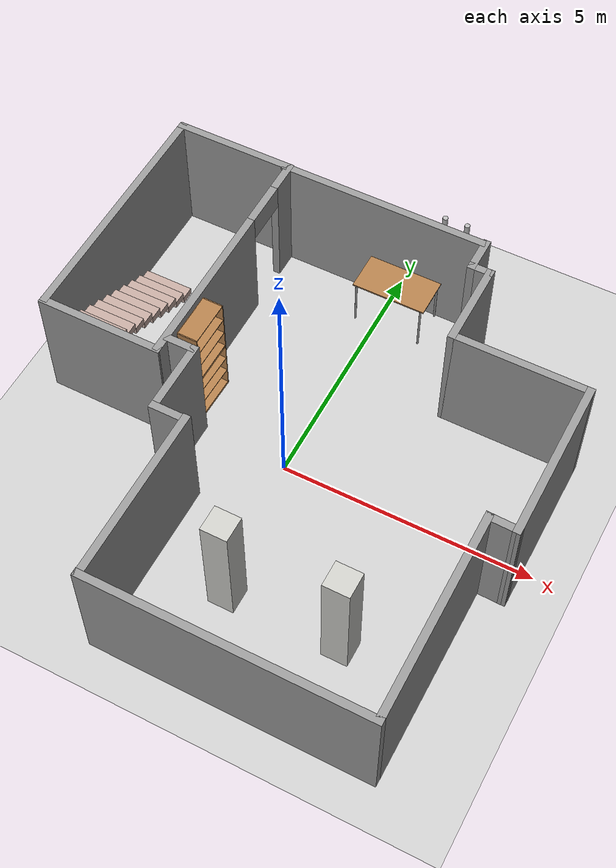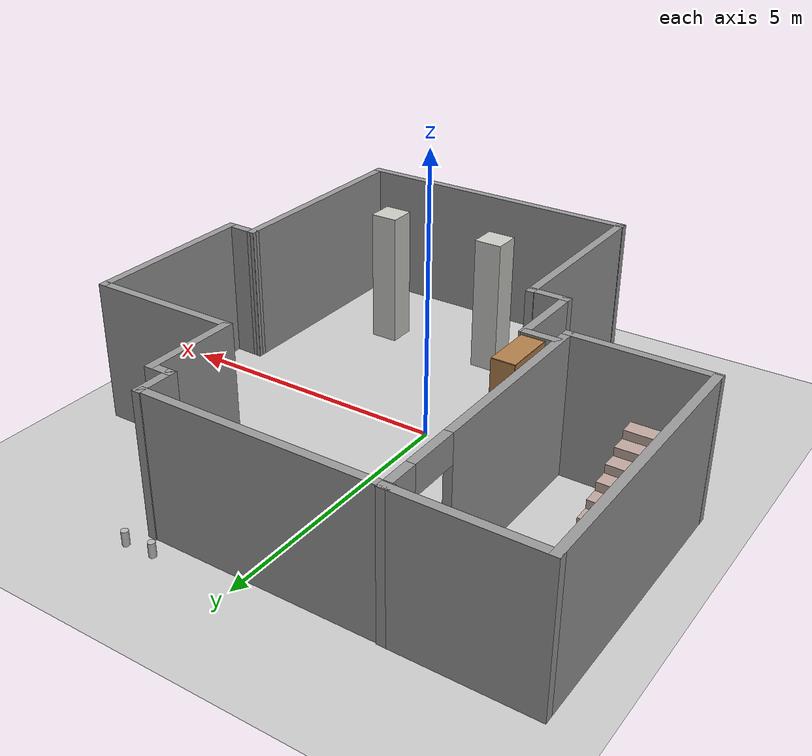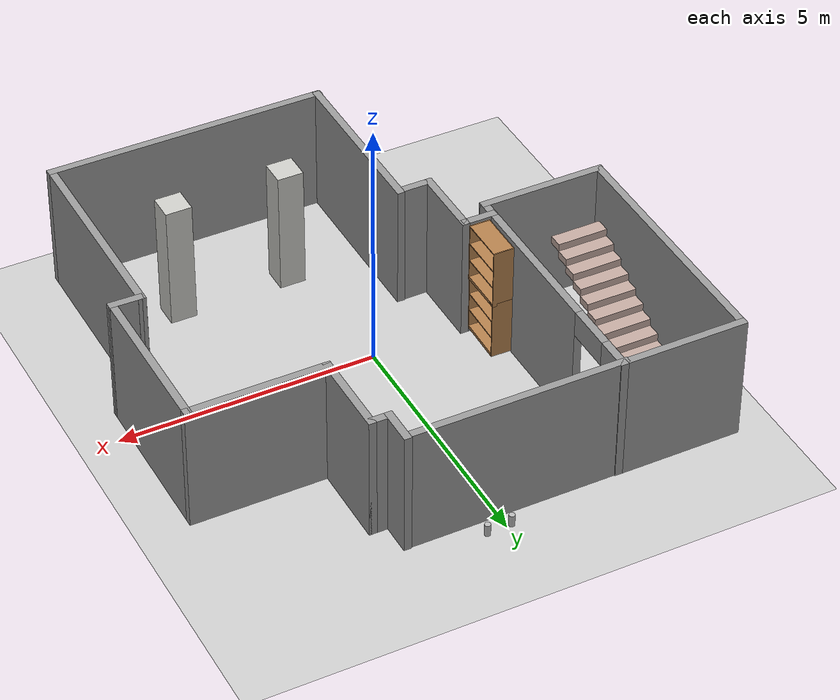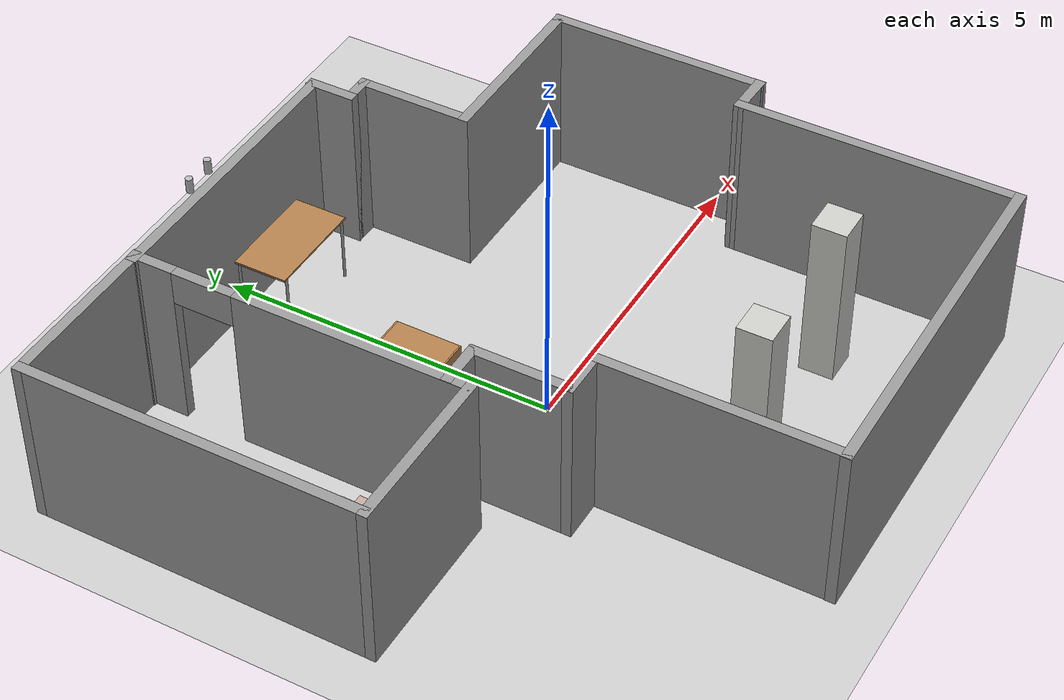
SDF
<sdf version="1.6">
 <world name="default">
  <light name="sun" type="directional">
   <pose>0 0 10 0 -0 0</pose>
   <diffuse>0.8 0.8 0.8 1</diffuse>
   <specular>0.1 0.1 0.1 1</specular>
   <attenuation>
    <range>1000</range>
    <constant>0.9</constant>
    <linear>0.01</linear>
    <quadratic>0.001</quadratic>
   </attenuation>
   <direction>-0.5 0.5 -1</direction>
  </light>
  <model name="ground_plane">
   <static>1</static>
   <link name="link">
    <collision name="collision">
     <geometry><plane><normal>0 0 1</normal><size>100 100</size></plane></geometry>
     <surface><friction><ode><mu>100</mu><mu2>50</mu2></ode></friction></surface>
    </collision>
    <visual name="visual">
     <cast_shadows>0</cast_shadows>
     <geometry><plane><normal>0 0 1</normal><size>100 100</size></plane></geometry>
     <material>
      <script><uri>file://media/materials/scripts/gazebo.material</uri><name>Gazebo/Grey</name></script>
     </material>
    </visual>
   </link>
  </model>
  <gravity>0 0 -9.8</gravity>
  <magnetic_field>6e-06 2.3e-05 -4.2e-05</magnetic_field>
  <atmosphere type="adiabatic"/>
  <physics name="default_physics" default="0" type="ode">
   <max_step_size>0.001</max_step_size>
   <real_time_factor>1</real_time_factor>
   <real_time_update_rate>1000</real_time_update_rate>
  </physics>
  <scene><ambient>0.4 0.4 0.4 1</ambient><background>0.7 0.7 0.7 1</background><shadows>1</shadows></scene>
  <spherical_coordinates>
   <surface_model>EARTH_WGS84</surface_model>
   <latitude_deg>0</latitude_deg>
   <longitude_deg>0</longitude_deg>
   <elevation>0</elevation>
   <heading_deg>0</heading_deg>
  </spherical_coordinates>
  <model name="amtc">
   <link name="Stairs_2">
    <visual name="Stairs_2_Visual_0">
     <pose>-4.10209 2.63631 0.075 0 -0 0</pose>
     <geometry><box><size>1 0.275 0.15</size></box></geometry>
     <material>
      <script><uri>file://media/materials/scripts/gazebo.material</uri><name>Gazebo/Grey</name></script>
      <ambient>0.760784 0.662745 0.627451 1</ambient>
      <diffuse>0.7 0.7 0.7 1</diffuse>
      <specular>0.01 0.01 0.01 1</specular>
      <emissive>0 0 0 1</emissive>
     </material>
     <meta><layer>0</layer></meta>
    </visual>
    <visual name="Stairs_2_Visual_7">
     <pose>-4.10209 0.711315 1.125 0 -0 0</pose>
     <geometry><box><size>1 0.275 0.15</size></box></geometry>
     <material>
      <script><uri>file://media/materials/scripts/gazebo.material</uri><name>Gazebo/Grey</name></script>
      <ambient>0.760784 0.662745 0.627451 1</ambient>
      <diffuse>0.7 0.7 0.7 1</diffuse>
      <specular>0.01 0.01 0.01 1</specular>
      <emissive>0 0 0 1</emissive>
     </material>
     <meta><layer>0</layer></meta>
    </visual>
    <visual name="Stairs_2_Visual_8">
     <pose>-4.10209 0.436315 1.275 0 -0 0</pose>
     <geometry><box><size>1 0.275 0.15</size></box></geometry>
     <material>
      <script><uri>file://media/materials/scripts/gazebo.material</uri><name>Gazebo/Grey</name></script>
      <ambient>0.760784 0.662745 0.627451 1</ambient>
      <diffuse>0.7 0.7 0.7 1</diffuse>
      <specular>0.01 0.01 0.01 1</specular>
      <emissive>0 0 0 1</emissive>
     </material>
     <meta><layer>0</layer></meta>
    </visual>
    <visual name="Stairs_2_Visual_6">
     <pose>-4.10209 0.986315 0.975 0 -0 0</pose>
     <geometry><box><size>1 0.275 0.15</size></box></geometry>
     <material>
      <script><uri>file://media/materials/scripts/gazebo.material</uri><name>Gazebo/Grey</name></script>
      <ambient>0.760784 0.662745 0.627451 1</ambient>
      <diffuse>0.7 0.7 0.7 1</diffuse>
      <specular>0.01 0.01 0.01 1</specular>
      <emissive>0 0 0 1</emissive>
     </material>
     <meta><layer>0</layer></meta>
    </visual>
    <visual name="Stairs_2_Visual_5">
     <pose>-4.10209 1.26131 0.825 0 -0 0</pose>
     <geometry><box><size>1 0.275 0.15</size></box></geometry>
     <material>
      <script><uri>file://media/materials/scripts/gazebo.material</uri><name>Gazebo/Grey</name></script>
      <ambient>0.760784 0.662745 0.627451 1</ambient>
      <diffuse>0.7 0.7 0.7 1</diffuse>
      <specular>0.01 0.01 0.01 1</specular>
      <emissive>0 0 0 1</emissive>
     </material>
     <meta><layer>0</layer></meta>
    </visual>
    <visual name="Stairs_2_Visual_2">
     <pose>-4.10209 2.08631 0.375 0 -0 0</pose>
     <geometry><box><size>1 0.275 0.15</size></box></geometry>
     <material>
      <script><uri>file://media/materials/scripts/gazebo.material</uri><name>Gazebo/Grey</name></script>
      <ambient>0.760784 0.662745 0.627451 1</ambient>
      <diffuse>0.7 0.7 0.7 1</diffuse>
      <specular>0.01 0.01 0.01 1</specular>
      <emissive>0 0 0 1</emissive>
     </material>
     <meta><layer>0</layer></meta>
    </visual>
    <visual name="Stairs_2_Visual_4">
     <pose>-4.10209 1.53632 0.675 0 -0 0</pose>
     <geometry><box><size>1 0.275 0.15</size></box></geometry>
     <material>
      <script><uri>file://media/materials/scripts/gazebo.material</uri><name>Gazebo/Grey</name></script>
      <ambient>0.760784 0.662745 0.627451 1</ambient>
      <diffuse>0.7 0.7 0.7 1</diffuse>
      <specular>0.01 0.01 0.01 1</specular>
      <emissive>0 0 0 1</emissive>
     </material>
     <meta><layer>0</layer></meta>
    </visual>
    <visual name="Stairs_2_Visual_1">
     <pose>-4.10209 2.36131 0.225 0 -0 0</pose>
     <geometry><box><size>1 0.275 0.15</size></box></geometry>
     <material>
      <script><uri>file://media/materials/scripts/gazebo.material</uri><name>Gazebo/Grey</name></script>
      <ambient>0.760784 0.662745 0.627451 1</ambient>
      <diffuse>0.7 0.7 0.7 1</diffuse>
      <specular>0.01 0.01 0.01 1</specular>
      <emissive>0 0 0 1</emissive>
     </material>
     <meta><layer>0</layer></meta>
    </visual>
    <visual name="Stairs_2_Visual_9">
     <pose>-4.10209 0.161315 1.425 0 -0 0</pose>
     <geometry><box><size>1 0.275 0.15</size></box></geometry>
     <material>
      <script><uri>file://media/materials/scripts/gazebo.material</uri><name>Gazebo/Grey</name></script>
      <ambient>0.760784 0.662745 0.627451 1</ambient>
      <diffuse>0.7 0.7 0.7 1</diffuse>
      <specular>0.01 0.01 0.01 1</specular>
      <emissive>0 0 0 1</emissive>
     </material>
     <meta><layer>0</layer></meta>
    </visual>
    <visual name="Stairs_2_Visual_3">
     <pose>-4.10209 1.81132 0.525 0 -0 0</pose>
     <geometry><box><size>1 0.275 0.15</size></box></geometry>
     <material>
      <script><uri>file://media/materials/scripts/gazebo.material</uri><name>Gazebo/Grey</name></script>
      <ambient>0.760784 0.662745 0.627451 1</ambient>
      <diffuse>0.7 0.7 0.7 1</diffuse>
      <specular>0.01 0.01 0.01 1</specular>
      <emissive>0 0 0 1</emissive>
     </material>
     <meta><layer>0</layer></meta>
    </visual>
    <collision name="Stairs_2_Collision_1">
     <pose>-4.10209 2.36131 0.225 0 -0 0</pose>
     <geometry><box><size>1 0.275 0.15</size></box></geometry>
     <surface>
      <friction>
       <ode><mu>1</mu><mu2>1</mu2><fdir1>0 0 0</fdir1><slip1>0</slip1><slip2>0</slip2></ode>
       <torsional>
        <coefficient>1</coefficient>
        <patch_radius>0</patch_radius>
        <surface_radius>0</surface_radius>
        <use_patch_radius>1</use_patch_radius>
        <ode><slip>0</slip></ode>
       </torsional>
      </friction>
      <bounce><restitution_coefficient>0</restitution_coefficient><threshold>1e+06</threshold></bounce>
      <contact>
       <collide_without_contact>0</collide_without_contact>
       <collide_without_contact_bitmask>1</collide_without_contact_bitmask>
       <collide_bitmask>1</collide_bitmask>
       <ode>
        <soft_cfm>0</soft_cfm>
        <soft_erp>0.2</soft_erp>
        <kp>1e+13</kp>
        <kd>1</kd>
        <max_vel>0.01</max_vel>
        <min_depth>0</min_depth>
       </ode>
       <bullet>
        <split_impulse>1</split_impulse>
        <split_impulse_penetration_threshold>-0.01</split_impulse_penetration_threshold>
        <soft_cfm>0</soft_cfm>
        <soft_erp>0.2</soft_erp>
        <kp>1e+13</kp>
        <kd>1</kd>
       </bullet>
      </contact>
     </surface>
    </collision>
    <collision name="Stairs_2_Collision_2">
     <pose>-4.10209 2.08631 0.375 0 -0 0</pose>
     <geometry><box><size>1 0.275 0.15</size></box></geometry>
     <surface>
      <friction>
       <ode><mu>1</mu><mu2>1</mu2><fdir1>0 0 0</fdir1><slip1>0</slip1><slip2>0</slip2></ode>
       <torsional>
        <coefficient>1</coefficient>
        <patch_radius>0</patch_radius>
        <surface_radius>0</surface_radius>
        <use_patch_radius>1</use_patch_radius>
        <ode><slip>0</slip></ode>
       </torsional>
      </friction>
      <bounce><restitution_coefficient>0</restitution_coefficient><threshold>1e+06</threshold></bounce>
      <contact>
       <collide_without_contact>0</collide_without_contact>
       <collide_without_contact_bitmask>1</collide_without_contact_bitmask>
       <collide_bitmask>1</collide_bitmask>
       <ode>
        <soft_cfm>0</soft_cfm>
        <soft_erp>0.2</soft_erp>
        <kp>1e+13</kp>
        <kd>1</kd>
        <max_vel>0.01</max_vel>
        <min_depth>0</min_depth>
       </ode>
       <bullet>
        <split_impulse>1</split_impulse>
        <split_impulse_penetration_threshold>-0.01</split_impulse_penetration_threshold>
        <soft_cfm>0</soft_cfm>
        <soft_erp>0.2</soft_erp>
        <kp>1e+13</kp>
        <kd>1</kd>
       </bullet>
      </contact>
     </surface>
    </collision>
    <collision name="Stairs_2_Collision_3">
     <pose>-4.10209 1.81132 0.525 0 -0 0</pose>
     <geometry><box><size>1 0.275 0.15</size></box></geometry>
     <surface>
      <friction>
       <ode><mu>1</mu><mu2>1</mu2><fdir1>0 0 0</fdir1><slip1>0</slip1><slip2>0</slip2></ode>
       <torsional>
        <coefficient>1</coefficient>
        <patch_radius>0</patch_radius>
        <surface_radius>0</surface_radius>
        <use_patch_radius>1</use_patch_radius>
        <ode><slip>0</slip></ode>
       </torsional>
      </friction>
      <bounce><restitution_coefficient>0</restitution_coefficient><threshold>1e+06</threshold></bounce>
      <contact>
       <collide_without_contact>0</collide_without_contact>
       <collide_without_contact_bitmask>1</collide_without_contact_bitmask>
       <collide_bitmask>1</collide_bitmask>
       <ode>
        <soft_cfm>0</soft_cfm>
        <soft_erp>0.2</soft_erp>
        <kp>1e+13</kp>
        <kd>1</kd>
        <max_vel>0.01</max_vel>
        <min_depth>0</min_depth>
       </ode>
       <bullet>
        <split_impulse>1</split_impulse>
        <split_impulse_penetration_threshold>-0.01</split_impulse_penetration_threshold>
        <soft_cfm>0</soft_cfm>
        <soft_erp>0.2</soft_erp>
        <kp>1e+13</kp>
        <kd>1</kd>
       </bullet>
      </contact>
     </surface>
    </collision>
    <collision name="Stairs_2_Collision_0">
     <pose>-4.10209 2.63631 0.075 0 -0 0</pose>
     <geometry><box><size>1 0.275 0.15</size></box></geometry>
     <surface>
      <friction>
       <ode><mu>1</mu><mu2>1</mu2><fdir1>0 0 0</fdir1><slip1>0</slip1><slip2>0</slip2></ode>
       <torsional>
        <coefficient>1</coefficient>
        <patch_radius>0</patch_radius>
        <surface_radius>0</surface_radius>
        <use_patch_radius>1</use_patch_radius>
        <ode><slip>0</slip></ode>
       </torsional>
      </friction>
      <bounce><restitution_coefficient>0</restitution_coefficient><threshold>1e+06</threshold></bounce>
      <contact>
       <collide_without_contact>0</collide_without_contact>
       <collide_without_contact_bitmask>1</collide_without_contact_bitmask>
       <collide_bitmask>1</collide_bitmask>
       <ode>
        <soft_cfm>0</soft_cfm>
        <soft_erp>0.2</soft_erp>
        <kp>1e+13</kp>
        <kd>1</kd>
        <max_vel>0.01</max_vel>
        <min_depth>0</min_depth>
       </ode>
       <bullet>
        <split_impulse>1</split_impulse>
        <split_impulse_penetration_threshold>-0.01</split_impulse_penetration_threshold>
        <soft_cfm>0</soft_cfm>
        <soft_erp>0.2</soft_erp>
        <kp>1e+13</kp>
        <kd>1</kd>
       </bullet>
      </contact>
     </surface>
    </collision>
    <collision name="Stairs_2_Collision_4">
     <pose>-4.10209 1.53632 0.675 0 -0 0</pose>
     <geometry><box><size>1 0.275 0.15</size></box></geometry>
     <surface>
      <friction>
       <ode><mu>1</mu><mu2>1</mu2><fdir1>0 0 0</fdir1><slip1>0</slip1><slip2>0</slip2></ode>
       <torsional>
        <coefficient>1</coefficient>
        <patch_radius>0</patch_radius>
        <surface_radius>0</surface_radius>
        <use_patch_radius>1</use_patch_radius>
        <ode><slip>0</slip></ode>
       </torsional>
      </friction>
      <bounce><restitution_coefficient>0</restitution_coefficient><threshold>1e+06</threshold></bounce>
      <contact>
       <collide_without_contact>0</collide_without_contact>
       <collide_without_contact_bitmask>1</collide_without_contact_bitmask>
       <collide_bitmask>1</collide_bitmask>
       <ode>
        <soft_cfm>0</soft_cfm>
        <soft_erp>0.2</soft_erp>
        <kp>1e+13</kp>
        <kd>1</kd>
        <max_vel>0.01</max_vel>
        <min_depth>0</min_depth>
       </ode>
       <bullet>
        <split_impulse>1</split_impulse>
        <split_impulse_penetration_threshold>-0.01</split_impulse_penetration_threshold>
        <soft_cfm>0</soft_cfm>
        <soft_erp>0.2</soft_erp>
        <kp>1e+13</kp>
        <kd>1</kd>
       </bullet>
      </contact>
     </surface>
    </collision>
    <collision name="Stairs_2_Collision_7">
     <pose>-4.10209 0.711315 1.125 0 -0 0</pose>
     <geometry><box><size>1 0.275 0.15</size></box></geometry>
     <surface>
      <friction>
       <ode><mu>1</mu><mu2>1</mu2><fdir1>0 0 0</fdir1><slip1>0</slip1><slip2>0</slip2></ode>
       <torsional>
        <coefficient>1</coefficient>
        <patch_radius>0</patch_radius>
        <surface_radius>0</surface_radius>
        <use_patch_radius>1</use_patch_radius>
        <ode><slip>0</slip></ode>
       </torsional>
      </friction>
      <bounce><restitution_coefficient>0</restitution_coefficient><threshold>1e+06</threshold></bounce>
      <contact>
       <collide_without_contact>0</collide_without_contact>
       <collide_without_contact_bitmask>1</collide_without_contact_bitmask>
       <collide_bitmask>1</collide_bitmask>
       <ode>
        <soft_cfm>0</soft_cfm>
        <soft_erp>0.2</soft_erp>
        <kp>1e+13</kp>
        <kd>1</kd>
        <max_vel>0.01</max_vel>
        <min_depth>0</min_depth>
       </ode>
       <bullet>
        <split_impulse>1</split_impulse>
        <split_impulse_penetration_threshold>-0.01</split_impulse_penetration_threshold>
        <soft_cfm>0</soft_cfm>
        <soft_erp>0.2</soft_erp>
        <kp>1e+13</kp>
        <kd>1</kd>
       </bullet>
      </contact>
     </surface>
    </collision>
    <collision name="Stairs_2_Collision_6">
     <pose>-4.10209 0.986315 0.975 0 -0 0</pose>
     <geometry><box><size>1 0.275 0.15</size></box></geometry>
     <surface>
      <friction>
       <ode><mu>1</mu><mu2>1</mu2><fdir1>0 0 0</fdir1><slip1>0</slip1><slip2>0</slip2></ode>
       <torsional>
        <coefficient>1</coefficient>
        <patch_radius>0</patch_radius>
        <surface_radius>0</surface_radius>
        <use_patch_radius>1</use_patch_radius>
        <ode><slip>0</slip></ode>
       </torsional>
      </friction>
      <bounce><restitution_coefficient>0</restitution_coefficient><threshold>1e+06</threshold></bounce>
      <contact>
       <collide_without_contact>0</collide_without_contact>
       <collide_without_contact_bitmask>1</collide_without_contact_bitmask>
       <collide_bitmask>1</collide_bitmask>
       <ode>
        <soft_cfm>0</soft_cfm>
        <soft_erp>0.2</soft_erp>
        <kp>1e+13</kp>
        <kd>1</kd>
        <max_vel>0.01</max_vel>
        <min_depth>0</min_depth>
       </ode>
       <bullet>
        <split_impulse>1</split_impulse>
        <split_impulse_penetration_threshold>-0.01</split_impulse_penetration_threshold>
        <soft_cfm>0</soft_cfm>
        <soft_erp>0.2</soft_erp>
        <kp>1e+13</kp>
        <kd>1</kd>
       </bullet>
      </contact>
     </surface>
    </collision>
    <collision name="Stairs_2_Collision_8">
     <pose>-4.10209 0.436315 1.275 0 -0 0</pose>
     <geometry><box><size>1 0.275 0.15</size></box></geometry>
     <surface>
      <friction>
       <ode><mu>1</mu><mu2>1</mu2><fdir1>0 0 0</fdir1><slip1>0</slip1><slip2>0</slip2></ode>
       <torsional>
        <coefficient>1</coefficient>
        <patch_radius>0</patch_radius>
        <surface_radius>0</surface_radius>
        <use_patch_radius>1</use_patch_radius>
        <ode><slip>0</slip></ode>
       </torsional>
      </friction>
      <bounce><restitution_coefficient>0</restitution_coefficient><threshold>1e+06</threshold></bounce>
      <contact>
       <collide_without_contact>0</collide_without_contact>
       <collide_without_contact_bitmask>1</collide_without_contact_bitmask>
       <collide_bitmask>1</collide_bitmask>
       <ode>
        <soft_cfm>0</soft_cfm>
        <soft_erp>0.2</soft_erp>
        <kp>1e+13</kp>
        <kd>1</kd>
        <max_vel>0.01</max_vel>
        <min_depth>0</min_depth>
       </ode>
       <bullet>
        <split_impulse>1</split_impulse>
        <split_impulse_penetration_threshold>-0.01</split_impulse_penetration_threshold>
        <soft_cfm>0</soft_cfm>
        <soft_erp>0.2</soft_erp>
        <kp>1e+13</kp>
        <kd>1</kd>
       </bullet>
      </contact>
     </surface>
    </collision>
    <collision name="Stairs_2_Collision_9">
     <pose>-4.10209 0.161315 1.425 0 -0 0</pose>
     <geometry><box><size>1 0.275 0.15</size></box></geometry>
     <surface>
      <friction>
       <ode><mu>1</mu><mu2>1</mu2><fdir1>0 0 0</fdir1><slip1>0</slip1><slip2>0</slip2></ode>
       <torsional>
        <coefficient>1</coefficient>
        <patch_radius>0</patch_radius>
        <surface_radius>0</surface_radius>
        <use_patch_radius>1</use_patch_radius>
        <ode><slip>0</slip></ode>
       </torsional>
      </friction>
      <bounce><restitution_coefficient>0</restitution_coefficient><threshold>1e+06</threshold></bounce>
      <contact>
       <collide_without_contact>0</collide_without_contact>
       <collide_without_contact_bitmask>1</collide_without_contact_bitmask>
       <collide_bitmask>1</collide_bitmask>
       <ode>
        <soft_cfm>0</soft_cfm>
        <soft_erp>0.2</soft_erp>
        <kp>1e+13</kp>
        <kd>1</kd>
        <max_vel>0.01</max_vel>
        <min_depth>0</min_depth>
       </ode>
       <bullet>
        <split_impulse>1</split_impulse>
        <split_impulse_penetration_threshold>-0.01</split_impulse_penetration_threshold>
        <soft_cfm>0</soft_cfm>
        <soft_erp>0.2</soft_erp>
        <kp>1e+13</kp>
        <kd>1</kd>
       </bullet>
      </contact>
     </surface>
    </collision>
    <collision name="Stairs_2_Collision_5">
     <pose>-4.10209 1.26131 0.825 0 -0 0</pose>
     <geometry><box><size>1 0.275 0.15</size></box></geometry>
     <surface>
      <friction>
       <ode><mu>1</mu><mu2>1</mu2><fdir1>0 0 0</fdir1><slip1>0</slip1><slip2>0</slip2></ode>
       <torsional>
        <coefficient>1</coefficient>
        <patch_radius>0</patch_radius>
        <surface_radius>0</surface_radius>
        <use_patch_radius>1</use_patch_radius>
        <ode><slip>0</slip></ode>
       </torsional>
      </friction>
      <bounce><restitution_coefficient>0</restitution_coefficient><threshold>1e+06</threshold></bounce>
      <contact>
       <collide_without_contact>0</collide_without_contact>
       <collide_without_contact_bitmask>1</collide_without_contact_bitmask>
       <collide_bitmask>1</collide_bitmask>
       <ode>
        <soft_cfm>0</soft_cfm>
        <soft_erp>0.2</soft_erp>
        <kp>1e+13</kp>
        <kd>1</kd>
        <max_vel>0.01</max_vel>
        <min_depth>0</min_depth>
       </ode>
       <bullet>
        <split_impulse>1</split_impulse>
        <split_impulse_penetration_threshold>-0.01</split_impulse_penetration_threshold>
        <soft_cfm>0</soft_cfm>
        <soft_erp>0.2</soft_erp>
        <kp>1e+13</kp>
        <kd>1</kd>
       </bullet>
      </contact>
     </surface>
    </collision>
   </link>
   <link name="Wall_18">
    <pose>-4.70094 2.21854 0 0 0 -1.5708</pose>
    <visual name="Wall_18_Visual">
     <pose>0 0 1.25 0 -0 0</pose>
     <geometry><box><size>5 0.15 2.5</size></box></geometry>
     <material>
      <script><uri>file://media/materials/scripts/gazebo.material</uri><name>Gazebo/Grey</name></script>
      <ambient>1 1 1 1</ambient>
      <diffuse>0.7 0.7 0.7 1</diffuse>
      <specular>0.01 0.01 0.01 1</specular>
      <emissive>0 0 0 1</emissive>
     </material>
     <meta><layer>0</layer></meta>
    </visual>
    <collision name="Wall_18_Collision">
     <pose>0 0 1.25 0 -0 0</pose>
     <geometry><box><size>5 0.15 2.5</size></box></geometry>
     <surface>
      <friction>
       <ode><mu>1</mu><mu2>1</mu2><fdir1>0 0 0</fdir1><slip1>0</slip1><slip2>0</slip2></ode>
       <torsional>
        <coefficient>1</coefficient>
        <patch_radius>0</patch_radius>
        <surface_radius>0</surface_radius>
        <use_patch_radius>1</use_patch_radius>
        <ode><slip>0</slip></ode>
       </torsional>
      </friction>
      <bounce><restitution_coefficient>0</restitution_coefficient><threshold>1e+06</threshold></bounce>
      <contact>
       <collide_without_contact>0</collide_without_contact>
       <collide_without_contact_bitmask>1</collide_without_contact_bitmask>
       <collide_bitmask>1</collide_bitmask>
       <ode>
        <soft_cfm>0</soft_cfm>
        <soft_erp>0.2</soft_erp>
        <kp>1e+13</kp>
        <kd>1</kd>
        <max_vel>0.01</max_vel>
        <min_depth>0</min_depth>
       </ode>
       <bullet>
        <split_impulse>1</split_impulse>
        <split_impulse_penetration_threshold>-0.01</split_impulse_penetration_threshold>
        <soft_cfm>0</soft_cfm>
        <soft_erp>0.2</soft_erp>
        <kp>1e+13</kp>
        <kd>1</kd>
       </bullet>
      </contact>
     </surface>
    </collision>
   </link>
   <link name="Wall_19">
    <pose>-3.5281 -0.244815 0 0 -0 0</pose>
    <visual name="Wall_19_Visual">
     <pose>0 0 1.25 0 -0 0</pose>
     <geometry><box><size>2.5 0.15 2.5</size></box></geometry>
     <material>
      <script><uri>file://media/materials/scripts/gazebo.material</uri><name>Gazebo/Grey</name></script>
      <ambient>1 1 1 1</ambient>
      <diffuse>0.7 0.7 0.7 1</diffuse>
      <specular>0.01 0.01 0.01 1</specular>
      <emissive>0 0 0 1</emissive>
     </material>
     <meta><layer>0</layer></meta>
    </visual>
    <collision name="Wall_19_Collision">
     <pose>0 0 1.25 0 -0 0</pose>
     <geometry><box><size>2.5 0.15 2.5</size></box></geometry>
     <surface>
      <friction>
       <ode><mu>1</mu><mu2>1</mu2><fdir1>0 0 0</fdir1><slip1>0</slip1><slip2>0</slip2></ode>
       <torsional>
        <coefficient>1</coefficient>
        <patch_radius>0</patch_radius>
        <surface_radius>0</surface_radius>
        <use_patch_radius>1</use_patch_radius>
        <ode><slip>0</slip></ode>
       </torsional>
      </friction>
      <bounce><restitution_coefficient>0</restitution_coefficient><threshold>1e+06</threshold></bounce>
      <contact>
       <collide_without_contact>0</collide_without_contact>
       <collide_without_contact_bitmask>1</collide_without_contact_bitmask>
       <collide_bitmask>1</collide_bitmask>
       <ode>
        <soft_cfm>0</soft_cfm>
        <soft_erp>0.2</soft_erp>
        <kp>1e+13</kp>
        <kd>1</kd>
        <max_vel>0.01</max_vel>
        <min_depth>0</min_depth>
       </ode>
       <bullet>
        <split_impulse>1</split_impulse>
        <split_impulse_penetration_threshold>-0.01</split_impulse_penetration_threshold>
        <soft_cfm>0</soft_cfm>
        <soft_erp>0.2</soft_erp>
        <kp>1e+13</kp>
        <kd>1</kd>
       </bullet>
      </contact>
     </surface>
    </collision>
   </link>
   <link name="Wall_21">
    <pose>-2.35094 2.21854 0 0 -0 1.5708</pose>
    <visual name="Wall_21_Visual_2">
     <pose>1.38064 0 2.25 0 -0 0</pose>
     <geometry><box><size>0.9 0.15 0.5</size></box></geometry>
     <material>
      <script><uri>file://media/materials/scripts/gazebo.material</uri><name>Gazebo/Grey</name></script>
      <ambient>1 1 1 1</ambient>
      <diffuse>0.7 0.7 0.7 1</diffuse>
      <specular>0.01 0.01 0.01 1</specular>
      <emissive>0 0 0 1</emissive>
     </material>
     <meta><layer>0</layer></meta>
    </visual>
    <visual name="Wall_21_Visual_0">
     <pose>-0.78468 0 1.25 0 -0 0</pose>
     <geometry><box><size>3.43064 0.15 2.5</size></box></geometry>
     <material>
      <script><uri>file://media/materials/scripts/gazebo.material</uri><name>Gazebo/Grey</name></script>
      <ambient>1 1 1 1</ambient>
      <diffuse>0.7 0.7 0.7 1</diffuse>
      <specular>0.01 0.01 0.01 1</specular>
      <emissive>0 0 0 1</emissive>
     </material>
     <meta><layer>0</layer></meta>
    </visual>
    <visual name="Wall_21_Visual_1">
     <pose>2.16532 0 1.25 0 -0 0</pose>
     <geometry><box><size>0.669361 0.15 2.5</size></box></geometry>
     <material>
      <script><uri>file://media/materials/scripts/gazebo.material</uri><name>Gazebo/Grey</name></script>
      <ambient>1 1 1 1</ambient>
      <diffuse>0.7 0.7 0.7 1</diffuse>
      <specular>0.01 0.01 0.01 1</specular>
      <emissive>0 0 0 1</emissive>
     </material>
     <meta><layer>0</layer></meta>
    </visual>
    <collision name="Wall_21_Collision_0">
     <pose>-0.78468 0 1.25 0 -0 0</pose>
     <geometry><box><size>3.43064 0.15 2.5</size></box></geometry>
     <surface>
      <friction>
       <ode><mu>1</mu><mu2>1</mu2><fdir1>0 0 0</fdir1><slip1>0</slip1><slip2>0</slip2></ode>
       <torsional>
        <coefficient>1</coefficient>
        <patch_radius>0</patch_radius>
        <surface_radius>0</surface_radius>
        <use_patch_radius>1</use_patch_radius>
        <ode><slip>0</slip></ode>
       </torsional>
      </friction>
      <bounce><restitution_coefficient>0</restitution_coefficient><threshold>1e+06</threshold></bounce>
      <contact>
       <collide_without_contact>0</collide_without_contact>
       <collide_without_contact_bitmask>1</collide_without_contact_bitmask>
       <collide_bitmask>1</collide_bitmask>
       <ode>
        <soft_cfm>0</soft_cfm>
        <soft_erp>0.2</soft_erp>
        <kp>1e+13</kp>
        <kd>1</kd>
        <max_vel>0.01</max_vel>
        <min_depth>0</min_depth>
       </ode>
       <bullet>
        <split_impulse>1</split_impulse>
        <split_impulse_penetration_threshold>-0.01</split_impulse_penetration_threshold>
        <soft_cfm>0</soft_cfm>
        <soft_erp>0.2</soft_erp>
        <kp>1e+13</kp>
        <kd>1</kd>
       </bullet>
      </contact>
     </surface>
    </collision>
    <collision name="Wall_21_Collision_1">
     <pose>2.16532 0 1.25 0 -0 0</pose>
     <geometry><box><size>0.669361 0.15 2.5</size></box></geometry>
     <surface>
      <friction>
       <ode><mu>1</mu><mu2>1</mu2><fdir1>0 0 0</fdir1><slip1>0</slip1><slip2>0</slip2></ode>
       <torsional>
        <coefficient>1</coefficient>
        <patch_radius>0</patch_radius>
        <surface_radius>0</surface_radius>
        <use_patch_radius>1</use_patch_radius>
        <ode><slip>0</slip></ode>
       </torsional>
      </friction>
      <bounce><restitution_coefficient>0</restitution_coefficient><threshold>1e+06</threshold></bounce>
      <contact>
       <collide_without_contact>0</collide_without_contact>
       <collide_without_contact_bitmask>1</collide_without_contact_bitmask>
       <collide_bitmask>1</collide_bitmask>
       <ode>
        <soft_cfm>0</soft_cfm>
        <soft_erp>0.2</soft_erp>
        <kp>1e+13</kp>
        <kd>1</kd>
        <max_vel>0.01</max_vel>
        <min_depth>0</min_depth>
       </ode>
       <bullet>
        <split_impulse>1</split_impulse>
        <split_impulse_penetration_threshold>-0.01</split_impulse_penetration_threshold>
        <soft_cfm>0</soft_cfm>
        <soft_erp>0.2</soft_erp>
        <kp>1e+13</kp>
        <kd>1</kd>
       </bullet>
      </contact>
     </surface>
    </collision>
    <collision name="Wall_21_Collision_2">
     <pose>1.38064 0 2.25 0 -0 0</pose>
     <geometry><box><size>0.9 0.15 0.5</size></box></geometry>
     <surface>
      <friction>
       <ode><mu>1</mu><mu2>1</mu2><fdir1>0 0 0</fdir1><slip1>0</slip1><slip2>0</slip2></ode>
       <torsional>
        <coefficient>1</coefficient>
        <patch_radius>0</patch_radius>
        <surface_radius>0</surface_radius>
        <use_patch_radius>1</use_patch_radius>
        <ode><slip>0</slip></ode>
       </torsional>
      </friction>
      <bounce><restitution_coefficient>0</restitution_coefficient><threshold>1e+06</threshold></bounce>
      <contact>
       <collide_without_contact>0</collide_without_contact>
       <collide_without_contact_bitmask>1</collide_without_contact_bitmask>
       <collide_bitmask>1</collide_bitmask>
       <ode>
        <soft_cfm>0</soft_cfm>
        <soft_erp>0.2</soft_erp>
        <kp>1e+13</kp>
        <kd>1</kd>
        <max_vel>0.01</max_vel>
        <min_depth>0</min_depth>
       </ode>
       <bullet>
        <split_impulse>1</split_impulse>
        <split_impulse_penetration_threshold>-0.01</split_impulse_penetration_threshold>
        <soft_cfm>0</soft_cfm>
        <soft_erp>0.2</soft_erp>
        <kp>1e+13</kp>
        <kd>1</kd>
       </bullet>
      </contact>
     </surface>
    </collision>
   </link>
   <link name="Wall_22">
    <pose>-3.52594 4.64354 0 0 -0 3.14159</pose>
    <visual name="Wall_22_Visual">
     <pose>0 0 1.25 0 -0 0</pose>
     <geometry><box><size>2.5 0.15 2.5</size></box></geometry>
     <material>
      <script><uri>file://media/materials/scripts/gazebo.material</uri><name>Gazebo/Grey</name></script>
      <ambient>1 1 1 1</ambient>
      <diffuse>0.7 0.7 0.7 1</diffuse>
      <specular>0.01 0.01 0.01 1</specular>
      <emissive>0 0 0 1</emissive>
     </material>
     <meta><layer>0</layer></meta>
    </visual>
    <collision name="Wall_22_Collision">
     <pose>0 0 1.25 0 -0 0</pose>
     <geometry><box><size>2.5 0.15 2.5</size></box></geometry>
     <surface>
      <friction>
       <ode><mu>1</mu><mu2>1</mu2><fdir1>0 0 0</fdir1><slip1>0</slip1><slip2>0</slip2></ode>
       <torsional>
        <coefficient>1</coefficient>
        <patch_radius>0</patch_radius>
        <surface_radius>0</surface_radius>
        <use_patch_radius>1</use_patch_radius>
        <ode><slip>0</slip></ode>
       </torsional>
      </friction>
      <bounce><restitution_coefficient>0</restitution_coefficient><threshold>1e+06</threshold></bounce>
      <contact>
       <collide_without_contact>0</collide_without_contact>
       <collide_without_contact_bitmask>1</collide_without_contact_bitmask>
       <collide_bitmask>1</collide_bitmask>
       <ode>
        <soft_cfm>0</soft_cfm>
        <soft_erp>0.2</soft_erp>
        <kp>1e+13</kp>
        <kd>1</kd>
        <max_vel>0.01</max_vel>
        <min_depth>0</min_depth>
       </ode>
       <bullet>
        <split_impulse>1</split_impulse>
        <split_impulse_penetration_threshold>-0.01</split_impulse_penetration_threshold>
        <soft_cfm>0</soft_cfm>
        <soft_erp>0.2</soft_erp>
        <kp>1e+13</kp>
        <kd>1</kd>
       </bullet>
      </contact>
     </surface>
    </collision>
   </link>
   <link name="Wall_24">
    <pose>-0.349165 4.62612 0 0 -0 0</pose>
    <inertial>
     <mass>1</mass>
     <inertia><ixx>1</ixx><ixy>0</ixy><ixz>0</ixz><iyy>1</iyy><iyz>0</iyz><izz>1</izz></inertia>
    </inertial>
    <visual name="Wall_24_Visual">
     <pose>0 0 1.25 0 -0 0</pose>
     <geometry><box><size>4.25 0.15 2.5</size></box></geometry>
     <material>
      <script><uri>file://media/materials/scripts/gazebo.material</uri><name>Gazebo/Grey</name></script>
      <ambient>1 1 1 1</ambient>
      <diffuse>0.7 0.7 0.7 1</diffuse>
      <specular>0.01 0.01 0.01 1</specular>
      <emissive>0 0 0 1</emissive>
      <shader type="vertex"><normal_map>__default__</normal_map></shader>
     </material>
     <meta><layer>0</layer></meta>
    </visual>
    <collision name="Wall_24_Collision">
     <pose>0 0 1.25 0 -0 0</pose>
     <geometry><box><size>4.25 0.15 2.5</size></box></geometry>
     <surface>
      <friction>
       <ode><mu>1</mu><mu2>1</mu2><fdir1>0 0 0</fdir1><slip1>0</slip1><slip2>0</slip2></ode>
       <torsional>
        <coefficient>1</coefficient>
        <patch_radius>0</patch_radius>
        <surface_radius>0</surface_radius>
        <use_patch_radius>1</use_patch_radius>
        <ode><slip>0</slip></ode>
       </torsional>
      </friction>
      <bounce><restitution_coefficient>0</restitution_coefficient><threshold>1e+06</threshold></bounce>
      <contact>
       <collide_without_contact>0</collide_without_contact>
       <collide_without_contact_bitmask>1</collide_without_contact_bitmask>
       <collide_bitmask>1</collide_bitmask>
       <ode>
        <soft_cfm>0</soft_cfm>
        <soft_erp>0.2</soft_erp>
        <kp>1e+13</kp>
        <kd>1</kd>
        <max_vel>0.01</max_vel>
        <min_depth>0</min_depth>
       </ode>
       <bullet>
        <split_impulse>1</split_impulse>
        <split_impulse_penetration_threshold>-0.01</split_impulse_penetration_threshold>
        <soft_cfm>0</soft_cfm>
        <soft_erp>0.2</soft_erp>
        <kp>1e+13</kp>
        <kd>1</kd>
       </bullet>
      </contact>
     </surface>
    </collision>
   </link>
   <link name="Wall_25">
    <pose>1.74906 4.34354 0 0 0 -1.5708</pose>
    <visual name="Wall_25_Visual">
     <pose>0 0 1.25 0 -0 0</pose>
     <geometry><box><size>0.75 0.15 2.5</size></box></geometry>
     <material>
      <script><uri>file://media/materials/scripts/gazebo.material</uri><name>Gazebo/Grey</name></script>
      <ambient>1 1 1 1</ambient>
      <diffuse>0.7 0.7 0.7 1</diffuse>
      <specular>0.01 0.01 0.01 1</specular>
      <emissive>0 0 0 1</emissive>
     </material>
     <meta><layer>0</layer></meta>
    </visual>
    <collision name="Wall_25_Collision">
     <pose>0 0 1.25 0 -0 0</pose>
     <geometry><box><size>0.75 0.15 2.5</size></box></geometry>
     <surface>
      <friction>
       <ode><mu>1</mu><mu2>1</mu2><fdir1>0 0 0</fdir1><slip1>0</slip1><slip2>0</slip2></ode>
       <torsional>
        <coefficient>1</coefficient>
        <patch_radius>0</patch_radius>
        <surface_radius>0</surface_radius>
        <use_patch_radius>1</use_patch_radius>
        <ode><slip>0</slip></ode>
       </torsional>
      </friction>
      <bounce><restitution_coefficient>0</restitution_coefficient><threshold>1e+06</threshold></bounce>
      <contact>
       <collide_without_contact>0</collide_without_contact>
       <collide_without_contact_bitmask>1</collide_without_contact_bitmask>
       <collide_bitmask>1</collide_bitmask>
       <ode>
        <soft_cfm>0</soft_cfm>
        <soft_erp>0.2</soft_erp>
        <kp>1e+13</kp>
        <kd>1</kd>
        <max_vel>0.01</max_vel>
        <min_depth>0</min_depth>
       </ode>
       <bullet>
        <split_impulse>1</split_impulse>
        <split_impulse_penetration_threshold>-0.01</split_impulse_penetration_threshold>
        <soft_cfm>0</soft_cfm>
        <soft_erp>0.2</soft_erp>
        <kp>1e+13</kp>
        <kd>1</kd>
       </bullet>
      </contact>
     </surface>
    </collision>
   </link>
   <link name="Wall_26">
    <pose>1.92406 4.04354 0 0 -0 0</pose>
    <visual name="Wall_26_Visual">
     <pose>0 0 1.25 0 -0 0</pose>
     <geometry><box><size>0.5 0.15 2.5</size></box></geometry>
     <material>
      <script><uri>file://media/materials/scripts/gazebo.material</uri><name>Gazebo/Grey</name></script>
      <ambient>1 1 1 1</ambient>
      <diffuse>0.7 0.7 0.7 1</diffuse>
      <specular>0.01 0.01 0.01 1</specular>
      <emissive>0 0 0 1</emissive>
     </material>
     <meta><layer>0</layer></meta>
    </visual>
    <collision name="Wall_26_Collision">
     <pose>0 0 1.25 0 -0 0</pose>
     <geometry><box><size>0.5 0.15 2.5</size></box></geometry>
     <surface>
      <friction>
       <ode><mu>1</mu><mu2>1</mu2><fdir1>0 0 0</fdir1><slip1>0</slip1><slip2>0</slip2></ode>
       <torsional>
        <coefficient>1</coefficient>
        <patch_radius>0</patch_radius>
        <surface_radius>0</surface_radius>
        <use_patch_radius>1</use_patch_radius>
        <ode><slip>0</slip></ode>
       </torsional>
      </friction>
      <bounce><restitution_coefficient>0</restitution_coefficient><threshold>1e+06</threshold></bounce>
      <contact>
       <collide_without_contact>0</collide_without_contact>
       <collide_without_contact_bitmask>1</collide_without_contact_bitmask>
       <collide_bitmask>1</collide_bitmask>
       <ode>
        <soft_cfm>0</soft_cfm>
        <soft_erp>0.2</soft_erp>
        <kp>1e+13</kp>
        <kd>1</kd>
        <max_vel>0.01</max_vel>
        <min_depth>0</min_depth>
       </ode>
       <bullet>
        <split_impulse>1</split_impulse>
        <split_impulse_penetration_threshold>-0.01</split_impulse_penetration_threshold>
        <soft_cfm>0</soft_cfm>
        <soft_erp>0.2</soft_erp>
        <kp>1e+13</kp>
        <kd>1</kd>
       </bullet>
      </contact>
     </surface>
    </collision>
   </link>
   <link name="Wall_29">
    <pose>2.09906 3.24354 0 0 0 -1.5708</pose>
    <visual name="Wall_29_Visual">
     <pose>0 0 1.25 0 -0 0</pose>
     <geometry><box><size>1.75 0.15 2.5</size></box></geometry>
     <material>
      <script><uri>file://media/materials/scripts/gazebo.material</uri><name>Gazebo/Grey</name></script>
      <ambient>1 1 1 1</ambient>
      <diffuse>0.7 0.7 0.7 1</diffuse>
      <specular>0.01 0.01 0.01 1</specular>
      <emissive>0 0 0 1</emissive>
     </material>
     <meta><layer>0</layer></meta>
    </visual>
    <collision name="Wall_29_Collision">
     <pose>0 0 1.25 0 -0 0</pose>
     <geometry><box><size>1.75 0.15 2.5</size></box></geometry>
     <surface>
      <friction>
       <ode><mu>1</mu><mu2>1</mu2><fdir1>0 0 0</fdir1><slip1>0</slip1><slip2>0</slip2></ode>
       <torsional>
        <coefficient>1</coefficient>
        <patch_radius>0</patch_radius>
        <surface_radius>0</surface_radius>
        <use_patch_radius>1</use_patch_radius>
        <ode><slip>0</slip></ode>
       </torsional>
      </friction>
      <bounce><restitution_coefficient>0</restitution_coefficient><threshold>1e+06</threshold></bounce>
      <contact>
       <collide_without_contact>0</collide_without_contact>
       <collide_without_contact_bitmask>1</collide_without_contact_bitmask>
       <collide_bitmask>1</collide_bitmask>
       <ode>
        <soft_cfm>0</soft_cfm>
        <soft_erp>0.2</soft_erp>
        <kp>1e+13</kp>
        <kd>1</kd>
        <max_vel>0.01</max_vel>
        <min_depth>0</min_depth>
       </ode>
       <bullet>
        <split_impulse>1</split_impulse>
        <split_impulse_penetration_threshold>-0.01</split_impulse_penetration_threshold>
        <soft_cfm>0</soft_cfm>
        <soft_erp>0.2</soft_erp>
        <kp>1e+13</kp>
        <kd>1</kd>
       </bullet>
      </contact>
     </surface>
    </collision>
   </link>
   <link name="Wall_30">
    <pose>3.39906 2.44354 0 0 -0 0</pose>
    <visual name="Wall_30_Visual">
     <pose>0 0 1.25 0 -0 0</pose>
     <geometry><box><size>2.75 0.15 2.5</size></box></geometry>
     <material>
      <script><uri>file://media/materials/scripts/gazebo.material</uri><name>Gazebo/Grey</name></script>
      <ambient>1 1 1 1</ambient>
      <diffuse>0.7 0.7 0.7 1</diffuse>
      <specular>0.01 0.01 0.01 1</specular>
      <emissive>0 0 0 1</emissive>
     </material>
     <meta><layer>0</layer></meta>
    </visual>
    <collision name="Wall_30_Collision">
     <pose>0 0 1.25 0 -0 0</pose>
     <geometry><box><size>2.75 0.15 2.5</size></box></geometry>
     <surface>
      <friction>
       <ode><mu>1</mu><mu2>1</mu2><fdir1>0 0 0</fdir1><slip1>0</slip1><slip2>0</slip2></ode>
       <torsional>
        <coefficient>1</coefficient>
        <patch_radius>0</patch_radius>
        <surface_radius>0</surface_radius>
        <use_patch_radius>1</use_patch_radius>
        <ode><slip>0</slip></ode>
       </torsional>
      </friction>
      <bounce><restitution_coefficient>0</restitution_coefficient><threshold>1e+06</threshold></bounce>
      <contact>
       <collide_without_contact>0</collide_without_contact>
       <collide_without_contact_bitmask>1</collide_without_contact_bitmask>
       <collide_bitmask>1</collide_bitmask>
       <ode>
        <soft_cfm>0</soft_cfm>
        <soft_erp>0.2</soft_erp>
        <kp>1e+13</kp>
        <kd>1</kd>
        <max_vel>0.01</max_vel>
        <min_depth>0</min_depth>
       </ode>
       <bullet>
        <split_impulse>1</split_impulse>
        <split_impulse_penetration_threshold>-0.01</split_impulse_penetration_threshold>
        <soft_cfm>0</soft_cfm>
        <soft_erp>0.2</soft_erp>
        <kp>1e+13</kp>
        <kd>1</kd>
       </bullet>
      </contact>
     </surface>
    </collision>
   </link>
   <link name="Wall_34">
    <pose>4.69909 0.893515 0 0 0 -1.57077</pose>
    <visual name="Wall_34_Visual">
     <pose>0 0 1.25 0 -0 0</pose>
     <geometry><box><size>3.25 0.15 2.5</size></box></geometry>
     <material>
      <script><uri>file://media/materials/scripts/gazebo.material</uri><name>Gazebo/Grey</name></script>
      <ambient>1 1 1 1</ambient>
      <diffuse>0.7 0.7 0.7 1</diffuse>
      <specular>0.01 0.01 0.01 1</specular>
      <emissive>0 0 0 1</emissive>
     </material>
     <meta><layer>0</layer></meta>
    </visual>
    <collision name="Wall_34_Collision">
     <pose>0 0 1.25 0 -0 0</pose>
     <geometry><box><size>3.25 0.15 2.5</size></box></geometry>
     <surface>
      <friction>
       <ode><mu>1</mu><mu2>1</mu2><fdir1>0 0 0</fdir1><slip1>0</slip1><slip2>0</slip2></ode>
       <torsional>
        <coefficient>1</coefficient>
        <patch_radius>0</patch_radius>
        <surface_radius>0</surface_radius>
        <use_patch_radius>1</use_patch_radius>
        <ode><slip>0</slip></ode>
       </torsional>
      </friction>
      <bounce><restitution_coefficient>0</restitution_coefficient><threshold>1e+06</threshold></bounce>
      <contact>
       <collide_without_contact>0</collide_without_contact>
       <collide_without_contact_bitmask>1</collide_without_contact_bitmask>
       <collide_bitmask>1</collide_bitmask>
       <ode>
        <soft_cfm>0</soft_cfm>
        <soft_erp>0.2</soft_erp>
        <kp>1e+13</kp>
        <kd>1</kd>
        <max_vel>0.01</max_vel>
        <min_depth>0</min_depth>
       </ode>
       <bullet>
        <split_impulse>1</split_impulse>
        <split_impulse_penetration_threshold>-0.01</split_impulse_penetration_threshold>
        <soft_cfm>0</soft_cfm>
        <soft_erp>0.2</soft_erp>
        <kp>1e+13</kp>
        <kd>1</kd>
       </bullet>
      </contact>
     </surface>
    </collision>
   </link>
   <link name="Wall_35">
    <pose>4.43465 -0.650022 0 0 -0 3.11708</pose>
    <visual name="Wall_35_Visual">
     <pose>0 0 1.25 0 -0 0</pose>
     <geometry><box><size>0.679107 0.15 2.5</size></box></geometry>
     <material>
      <script><uri>file://media/materials/scripts/gazebo.material</uri><name>Gazebo/Grey</name></script>
      <ambient>1 1 1 1</ambient>
      <diffuse>0.7 0.7 0.7 1</diffuse>
      <specular>0.01 0.01 0.01 1</specular>
      <emissive>0 0 0 1</emissive>
     </material>
     <meta><layer>0</layer></meta>
    </visual>
    <collision name="Wall_35_Collision">
     <pose>0 0 1.25 0 -0 0</pose>
     <geometry><box><size>0.679107 0.15 2.5</size></box></geometry>
     <surface>
      <friction>
       <ode><mu>1</mu><mu2>1</mu2><fdir1>0 0 0</fdir1><slip1>0</slip1><slip2>0</slip2></ode>
       <torsional>
        <coefficient>1</coefficient>
        <patch_radius>0</patch_radius>
        <surface_radius>0</surface_radius>
        <use_patch_radius>1</use_patch_radius>
        <ode><slip>0</slip></ode>
       </torsional>
      </friction>
      <bounce><restitution_coefficient>0</restitution_coefficient><threshold>1e+06</threshold></bounce>
      <contact>
       <collide_without_contact>0</collide_without_contact>
       <collide_without_contact_bitmask>1</collide_without_contact_bitmask>
       <collide_bitmask>1</collide_bitmask>
       <ode>
        <soft_cfm>0</soft_cfm>
        <soft_erp>0.2</soft_erp>
        <kp>1e+13</kp>
        <kd>1</kd>
        <max_vel>0.01</max_vel>
        <min_depth>0</min_depth>
       </ode>
       <bullet>
        <split_impulse>1</split_impulse>
        <split_impulse_penetration_threshold>-0.01</split_impulse_penetration_threshold>
        <soft_cfm>0</soft_cfm>
        <soft_erp>0.2</soft_erp>
        <kp>1e+13</kp>
        <kd>1</kd>
       </bullet>
      </contact>
     </surface>
    </collision>
   </link>
   <link name="Wall_59">
    <pose>0.388539 -2.79623 0 0 -0 0</pose>
    <inertial>
     <mass>1</mass>
     <inertia><ixx>1</ixx><ixy>0</ixy><ixz>0</ixz><iyy>1</iyy><iyz>0</iyz><izz>1</izz></inertia>
    </inertial>
    <visual name="Wall_59_Visual">
     <pose>0 0 1.25 0 -0 0</pose>
     <geometry><box><size>0.51 0.5 2.5</size></box></geometry>
     <material>
      <script><uri>file://media/materials/scripts/gazebo.material</uri><name>Gazebo/CeilingTiled</name></script>
      <ambient>1 1 1 1</ambient>
      <diffuse>1 1 1 1</diffuse>
      <specular>0 0 0 1</specular>
      <emissive>0 0 0 1</emissive>
      <shader type="vertex"><normal_map>__default__</normal_map></shader>
     </material>
     <meta><layer>0</layer></meta>
    </visual>
    <collision name="Wall_59_Collision">
     <pose>0 0 1.25 0 -0 0</pose>
     <geometry><box><size>0.51 0.5 2.5</size></box></geometry>
     <surface>
      <friction>
       <ode><mu>1</mu><mu2>1</mu2><fdir1>0 0 0</fdir1><slip1>0</slip1><slip2>0</slip2></ode>
       <torsional>
        <coefficient>1</coefficient>
        <patch_radius>0</patch_radius>
        <surface_radius>0</surface_radius>
        <use_patch_radius>1</use_patch_radius>
        <ode><slip>0</slip></ode>
       </torsional>
      </friction>
      <bounce><restitution_coefficient>0</restitution_coefficient><threshold>1e+06</threshold></bounce>
      <contact>
       <collide_without_contact>0</collide_without_contact>
       <collide_without_contact_bitmask>1</collide_without_contact_bitmask>
       <collide_bitmask>1</collide_bitmask>
       <ode>
        <soft_cfm>0</soft_cfm>
        <soft_erp>0.2</soft_erp>
        <kp>1e+13</kp>
        <kd>1</kd>
        <max_vel>0.01</max_vel>
        <min_depth>0</min_depth>
       </ode>
       <bullet>
        <split_impulse>1</split_impulse>
        <split_impulse_penetration_threshold>-0.01</split_impulse_penetration_threshold>
        <soft_cfm>0</soft_cfm>
        <soft_erp>0.2</soft_erp>
        <kp>1e+13</kp>
        <kd>1</kd>
       </bullet>
      </contact>
     </surface>
    </collision>
   </link>
   <link name="Wall_63">
    <pose>2.60498 -2.78179 0 0 -0 3.14159</pose>
    <visual name="Wall_63_Visual">
     <pose>0 0 1.25 0 -0 0</pose>
     <geometry><box><size>0.51 0.5 2.5</size></box></geometry>
     <material>
      <script><uri>file://media/materials/scripts/gazebo.material</uri><name>Gazebo/CeilingTiled</name></script>
      <ambient>1 1 1 1</ambient>
      <diffuse>1 1 1 1</diffuse>
      <specular>0 0 0 1</specular>
      <emissive>0 0 0 1</emissive>
     </material>
     <meta><layer>0</layer></meta>
    </visual>
    <collision name="Wall_63_Collision">
     <pose>0 0 1.25 0 -0 0</pose>
     <geometry><box><size>0.51 0.5 2.5</size></box></geometry>
     <surface>
      <friction>
       <ode><mu>1</mu><mu2>1</mu2><fdir1>0 0 0</fdir1><slip1>0</slip1><slip2>0</slip2></ode>
       <torsional>
        <coefficient>1</coefficient>
        <patch_radius>0</patch_radius>
        <surface_radius>0</surface_radius>
        <use_patch_radius>1</use_patch_radius>
        <ode><slip>0</slip></ode>
       </torsional>
      </friction>
      <bounce><restitution_coefficient>0</restitution_coefficient><threshold>1e+06</threshold></bounce>
      <contact>
       <collide_without_contact>0</collide_without_contact>
       <collide_without_contact_bitmask>1</collide_without_contact_bitmask>
       <collide_bitmask>1</collide_bitmask>
       <ode>
        <soft_cfm>0</soft_cfm>
        <soft_erp>0.2</soft_erp>
        <kp>1e+13</kp>
        <kd>1</kd>
        <max_vel>0.01</max_vel>
        <min_depth>0</min_depth>
       </ode>
       <bullet>
        <split_impulse>1</split_impulse>
        <split_impulse_penetration_threshold>-0.01</split_impulse_penetration_threshold>
        <soft_cfm>0</soft_cfm>
        <soft_erp>0.2</soft_erp>
        <kp>1e+13</kp>
        <kd>1</kd>
       </bullet>
      </contact>
     </surface>
    </collision>
   </link>
   <link name="Wall_65">
    <pose>4.17018 -2.64354 0 0 0 -1.5708</pose>
    <visual name="Wall_65_Visual">
     <pose>0 0 1.25 0 -0 0</pose>
     <geometry><box><size>4.15 0.15 2.5</size></box></geometry>
     <material>
      <script><uri>file://media/materials/scripts/gazebo.material</uri><name>Gazebo/Grey</name></script>
      <ambient>1 1 1 1</ambient>
      <diffuse>0.7 0.7 0.7 1</diffuse>
      <specular>0.01 0.01 0.01 1</specular>
      <emissive>0 0 0 1</emissive>
     </material>
     <meta><layer>0</layer></meta>
    </visual>
    <collision name="Wall_65_Collision">
     <pose>0 0 1.25 0 -0 0</pose>
     <geometry><box><size>4.15 0.15 2.5</size></box></geometry>
     <surface>
      <friction>
       <ode><mu>1</mu><mu2>1</mu2><fdir1>0 0 0</fdir1><slip1>0</slip1><slip2>0</slip2></ode>
       <torsional>
        <coefficient>1</coefficient>
        <patch_radius>0</patch_radius>
        <surface_radius>0</surface_radius>
        <use_patch_radius>1</use_patch_radius>
        <ode><slip>0</slip></ode>
       </torsional>
      </friction>
      <bounce><restitution_coefficient>0</restitution_coefficient><threshold>1e+06</threshold></bounce>
      <contact>
       <collide_without_contact>0</collide_without_contact>
       <collide_without_contact_bitmask>1</collide_without_contact_bitmask>
       <collide_bitmask>1</collide_bitmask>
       <ode>
        <soft_cfm>0</soft_cfm>
        <soft_erp>0.2</soft_erp>
        <kp>1e+13</kp>
        <kd>1</kd>
        <max_vel>0.01</max_vel>
        <min_depth>0</min_depth>
       </ode>
       <bullet>
        <split_impulse>1</split_impulse>
        <split_impulse_penetration_threshold>-0.01</split_impulse_penetration_threshold>
        <soft_cfm>0</soft_cfm>
        <soft_erp>0.2</soft_erp>
        <kp>1e+13</kp>
        <kd>1</kd>
       </bullet>
      </contact>
     </surface>
    </collision>
   </link>
   <link name="Wall_73">
    <pose>1.49518 -4.64354 0 0 -0 3.14159</pose>
    <visual name="Wall_73_Visual">
     <pose>0 0 1.25 0 -0 0</pose>
     <geometry><box><size>5.5 0.15 2.5</size></box></geometry>
     <material>
      <script><uri>file://media/materials/scripts/gazebo.material</uri><name>Gazebo/Grey</name></script>
      <ambient>1 1 1 1</ambient>
      <diffuse>0.7 0.7 0.7 1</diffuse>
      <specular>0.01 0.01 0.01 1</specular>
      <emissive>0 0 0 1</emissive>
     </material>
     <meta><layer>0</layer></meta>
    </visual>
    <collision name="Wall_73_Collision">
     <pose>0 0 1.25 0 -0 0</pose>
     <geometry><box><size>5.5 0.15 2.5</size></box></geometry>
     <surface>
      <friction>
       <ode><mu>1</mu><mu2>1</mu2><fdir1>0 0 0</fdir1><slip1>0</slip1><slip2>0</slip2></ode>
       <torsional>
        <coefficient>1</coefficient>
        <patch_radius>0</patch_radius>
        <surface_radius>0</surface_radius>
        <use_patch_radius>1</use_patch_radius>
        <ode><slip>0</slip></ode>
       </torsional>
      </friction>
      <bounce><restitution_coefficient>0</restitution_coefficient><threshold>1e+06</threshold></bounce>
      <contact>
       <collide_without_contact>0</collide_without_contact>
       <collide_without_contact_bitmask>1</collide_without_contact_bitmask>
       <collide_bitmask>1</collide_bitmask>
       <ode>
        <soft_cfm>0</soft_cfm>
        <soft_erp>0.2</soft_erp>
        <kp>1e+13</kp>
        <kd>1</kd>
        <max_vel>0.01</max_vel>
        <min_depth>0</min_depth>
       </ode>
       <bullet>
        <split_impulse>1</split_impulse>
        <split_impulse_penetration_threshold>-0.01</split_impulse_penetration_threshold>
        <soft_cfm>0</soft_cfm>
        <soft_erp>0.2</soft_erp>
        <kp>1e+13</kp>
        <kd>1</kd>
       </bullet>
      </contact>
     </surface>
    </collision>
   </link>
   <link name="Wall_74">
    <pose>-1.17086 -2.95153 0 0 -0 1.5708</pose>
    <visual name="Wall_74_Visual">
     <pose>0 0 1.25 0 -0 0</pose>
     <geometry><box><size>3.5 0.15 2.5</size></box></geometry>
     <material>
      <script><uri>file://media/materials/scripts/gazebo.material</uri><name>Gazebo/Grey</name></script>
      <ambient>1 1 1 1</ambient>
      <diffuse>0.7 0.7 0.7 1</diffuse>
      <specular>0.01 0.01 0.01 1</specular>
      <emissive>0 0 0 1</emissive>
     </material>
     <meta><layer>0</layer></meta>
    </visual>
    <collision name="Wall_74_Collision">
     <pose>0 0 1.25 0 -0 0</pose>
     <geometry><box><size>3.5 0.15 2.5</size></box></geometry>
     <surface>
      <friction>
       <ode><mu>1</mu><mu2>1</mu2><fdir1>0 0 0</fdir1><slip1>0</slip1><slip2>0</slip2></ode>
       <torsional>
        <coefficient>1</coefficient>
        <patch_radius>0</patch_radius>
        <surface_radius>0</surface_radius>
        <use_patch_radius>1</use_patch_radius>
        <ode><slip>0</slip></ode>
       </torsional>
      </friction>
      <bounce><restitution_coefficient>0</restitution_coefficient><threshold>1e+06</threshold></bounce>
      <contact>
       <collide_without_contact>0</collide_without_contact>
       <collide_without_contact_bitmask>1</collide_without_contact_bitmask>
       <collide_bitmask>1</collide_bitmask>
       <ode>
        <soft_cfm>0</soft_cfm>
        <soft_erp>0.2</soft_erp>
        <kp>1e+13</kp>
        <kd>1</kd>
        <max_vel>0.01</max_vel>
        <min_depth>0</min_depth>
       </ode>
       <bullet>
        <split_impulse>1</split_impulse>
        <split_impulse_penetration_threshold>-0.01</split_impulse_penetration_threshold>
        <soft_cfm>0</soft_cfm>
        <soft_erp>0.2</soft_erp>
        <kp>1e+13</kp>
        <kd>1</kd>
       </bullet>
      </contact>
     </surface>
    </collision>
   </link>
   <link name="Wall_78">
    <pose>-1.47982 -1.29354 0 0 -0 3.14159</pose>
    <visual name="Wall_78_Visual">
     <pose>0 0 1.25 0 -0 0</pose>
     <geometry><box><size>0.75 0.15 2.5</size></box></geometry>
     <material>
      <script><uri>file://media/materials/scripts/gazebo.material</uri><name>Gazebo/Grey</name></script>
      <ambient>1 1 1 1</ambient>
      <diffuse>0.7 0.7 0.7 1</diffuse>
      <specular>0.01 0.01 0.01 1</specular>
      <emissive>0 0 0 1</emissive>
     </material>
     <meta><layer>0</layer></meta>
    </visual>
    <collision name="Wall_78_Collision">
     <pose>0 0 1.25 0 -0 0</pose>
     <geometry><box><size>0.75 0.15 2.5</size></box></geometry>
     <surface>
      <friction>
       <ode><mu>1</mu><mu2>1</mu2><fdir1>0 0 0</fdir1><slip1>0</slip1><slip2>0</slip2></ode>
       <torsional>
        <coefficient>1</coefficient>
        <patch_radius>0</patch_radius>
        <surface_radius>0</surface_radius>
        <use_patch_radius>1</use_patch_radius>
        <ode><slip>0</slip></ode>
       </torsional>
      </friction>
      <bounce><restitution_coefficient>0</restitution_coefficient><threshold>1e+06</threshold></bounce>
      <contact>
       <collide_without_contact>0</collide_without_contact>
       <collide_without_contact_bitmask>1</collide_without_contact_bitmask>
       <collide_bitmask>1</collide_bitmask>
       <ode>
        <soft_cfm>0</soft_cfm>
        <soft_erp>0.2</soft_erp>
        <kp>1e+13</kp>
        <kd>1</kd>
        <max_vel>0.01</max_vel>
        <min_depth>0</min_depth>
       </ode>
       <bullet>
        <split_impulse>1</split_impulse>
        <split_impulse_penetration_threshold>-0.01</split_impulse_penetration_threshold>
        <soft_cfm>0</soft_cfm>
        <soft_erp>0.2</soft_erp>
        <kp>1e+13</kp>
        <kd>1</kd>
       </bullet>
      </contact>
     </surface>
    </collision>
   </link>
   <link name="Wall_79">
    <pose>-1.77982 -0.618537 0 0 -0 1.5708</pose>
    <visual name="Wall_79_Visual">
     <pose>0 0 1.25 0 -0 0</pose>
     <geometry><box><size>1.5 0.15 2.5</size></box></geometry>
     <material>
      <script><uri>file://media/materials/scripts/gazebo.material</uri><name>Gazebo/Grey</name></script>
      <ambient>1 1 1 1</ambient>
      <diffuse>0.7 0.7 0.7 1</diffuse>
      <specular>0.01 0.01 0.01 1</specular>
      <emissive>0 0 0 1</emissive>
     </material>
     <meta><layer>0</layer></meta>
    </visual>
    <collision name="Wall_79_Collision">
     <pose>0 0 1.25 0 -0 0</pose>
     <geometry><box><size>1.5 0.15 2.5</size></box></geometry>
     <surface>
      <friction>
       <ode><mu>1</mu><mu2>1</mu2><fdir1>0 0 0</fdir1><slip1>0</slip1><slip2>0</slip2></ode>
       <torsional>
        <coefficient>1</coefficient>
        <patch_radius>0</patch_radius>
        <surface_radius>0</surface_radius>
        <use_patch_radius>1</use_patch_radius>
        <ode><slip>0</slip></ode>
       </torsional>
      </friction>
      <bounce><restitution_coefficient>0</restitution_coefficient><threshold>1e+06</threshold></bounce>
      <contact>
       <collide_without_contact>0</collide_without_contact>
       <collide_without_contact_bitmask>1</collide_without_contact_bitmask>
       <collide_bitmask>1</collide_bitmask>
       <ode>
        <soft_cfm>0</soft_cfm>
        <soft_erp>0.2</soft_erp>
        <kp>1e+13</kp>
        <kd>1</kd>
        <max_vel>0.01</max_vel>
        <min_depth>0</min_depth>
       </ode>
       <bullet>
        <split_impulse>1</split_impulse>
        <split_impulse_penetration_threshold>-0.01</split_impulse_penetration_threshold>
        <soft_cfm>0</soft_cfm>
        <soft_erp>0.2</soft_erp>
        <kp>1e+13</kp>
        <kd>1</kd>
       </bullet>
      </contact>
     </surface>
    </collision>
   </link>
   <link name="Wall_82">
    <pose>-2.08044 0.056463 0 0 -0 3.14159</pose>
    <inertial>
     <inertia><ixx>nan</ixx><ixy>0</ixy><ixz>0</ixz><iyy>nan</iyy><iyz>0</iyz><izz>nan</izz></inertia>
     <mass>0</mass>
    </inertial>
    <visual name="Wall_82_Visual">
     <pose>0 0 1.25 0 -0 0</pose>
     <geometry><box><size>0.678343 0.15 2.5</size></box></geometry>
     <material>
      <script><uri>file://media/materials/scripts/gazebo.material</uri><name>Gazebo/Grey</name></script>
      <ambient>1 1 1 1</ambient>
      <diffuse>0.7 0.7 0.7 1</diffuse>
      <specular>0.01 0.01 0.01 1</specular>
      <emissive>0 0 0 1</emissive>
     </material>
     <meta><layer>0</layer></meta>
    </visual>
    <collision name="Wall_82_Collision">
     <pose>0 0 1.25 0 -0 0</pose>
     <geometry><box><size>0.678343 0.15 2.5</size></box></geometry>
     <surface>
      <friction>
       <ode><mu>1</mu><mu2>1</mu2><fdir1>0 0 0</fdir1><slip1>0</slip1><slip2>0</slip2></ode>
       <torsional>
        <coefficient>1</coefficient>
        <patch_radius>0</patch_radius>
        <surface_radius>0</surface_radius>
        <use_patch_radius>1</use_patch_radius>
        <ode><slip>0</slip></ode>
       </torsional>
      </friction>
      <bounce><restitution_coefficient>0</restitution_coefficient><threshold>1e+06</threshold></bounce>
      <contact>
       <collide_without_contact>0</collide_without_contact>
       <collide_without_contact_bitmask>1</collide_without_contact_bitmask>
       <collide_bitmask>1</collide_bitmask>
       <ode>
        <soft_cfm>0</soft_cfm>
        <soft_erp>0.2</soft_erp>
        <kp>1e+13</kp>
        <kd>1</kd>
        <max_vel>0.01</max_vel>
        <min_depth>0</min_depth>
       </ode>
       <bullet>
        <split_impulse>1</split_impulse>
        <split_impulse_penetration_threshold>-0.01</split_impulse_penetration_threshold>
        <soft_cfm>0</soft_cfm>
        <soft_erp>0.2</soft_erp>
        <kp>1e+13</kp>
        <kd>1</kd>
       </bullet>
      </contact>
     </surface>
    </collision>
   </link>
   <model name="bookshelf">
    <static>1</static>
    <link name="link">
     <inertial><mass>1</mass></inertial>
     <collision name="back">
      <pose>0 0.005 0.6 0 -0 0</pose>
      <geometry><box><size>0.9 0.01 1.2</size></box></geometry>
     </collision>
     <visual name="visual1">
      <pose>0 0.005 0.6 0 -0 0</pose>
      <geometry><box><size>0.9 0.01 1.2</size></box></geometry>
      <material>
       <script><uri>file://media/materials/scripts/gazebo.material</uri><name>Gazebo/Wood</name></script>
      </material>
     </visual>
     <collision name="left_side">
      <pose>0.45 -0.195 0.6 0 -0 0</pose>
      <geometry><box><size>0.02 0.4 1.2</size></box></geometry>
     </collision>
     <visual name="visual2">
      <pose>0.45 -0.195 0.6 0 -0 0</pose>
      <geometry><box><size>0.02 0.4 1.2</size></box></geometry>
      <material>
       <script><uri>file://media/materials/scripts/gazebo.material</uri><name>Gazebo/Wood</name></script>
      </material>
     </visual>
     <collision name="right_side">
      <pose>-0.45 -0.195 0.6 0 -0 0</pose>
      <geometry><box><size>0.02 0.4 1.2</size></box></geometry>
     </collision>
     <visual name="visual3">
      <pose>-0.45 -0.195 0.6 0 -0 0</pose>
      <geometry><box><size>0.02 0.4 1.2</size></box></geometry>
      <material>
       <script><uri>file://media/materials/scripts/gazebo.material</uri><name>Gazebo/Wood</name></script>
      </material>
     </visual>
     <collision name="bottom">
      <pose>0 -0.195 0.03 0 -0 0</pose>
      <geometry><box><size>0.88 0.4 0.06</size></box></geometry>
     </collision>
     <visual name="visual4">
      <pose>0 -0.195 0.03 0 -0 0</pose>
      <geometry><box><size>0.88 0.4 0.06</size></box></geometry>
      <material>
       <script><uri>file://media/materials/scripts/gazebo.material</uri><name>Gazebo/Wood</name></script>
      </material>
     </visual>
     <collision name="top">
      <pose>0 -0.195 1.19 0 -0 0</pose>
      <geometry><box><size>0.88 0.4 0.02</size></box></geometry>
     </collision>
     <visual name="visual5">
      <pose>0 -0.195 1.19 0 -0 0</pose>
      <geometry><box><size>0.88 0.4 0.02</size></box></geometry>
      <material>
       <script><uri>file://media/materials/scripts/gazebo.material</uri><name>Gazebo/Wood</name></script>
      </material>
     </visual>
     <collision name="low_shelf">
      <pose>0 -0.195 0.43 0 -0 0</pose>
      <geometry><box><size>0.88 0.4 0.02</size></box></geometry>
     </collision>
     <visual name="visual6">
      <pose>0 -0.195 0.43 0 -0 0</pose>
      <geometry><box><size>0.88 0.4 0.02</size></box></geometry>
      <material>
       <script><uri>file://media/materials/scripts/gazebo.material</uri><name>Gazebo/Wood</name></script>
      </material>
     </visual>
     <collision name="high_shelf">
      <pose>0 -0.195 0.8 0 -0 0</pose>
      <geometry><box><size>0.88 0.4 0.02</size></box></geometry>
     </collision>
     <visual name="visual7">
      <pose>0 -0.195 0.8 0 -0 0</pose>
      <geometry><box><size>0.88 0.4 0.02</size></box></geometry>
      <material>
       <script><uri>file://media/materials/scripts/gazebo.material</uri><name>Gazebo/Wood</name></script>
      </material>
     </visual>
    </link>
    <pose>-2.20096 0.669212 0.163551 0 -0 1.54625</pose>
   </model>
   <model name="bookshelf_0">
    <static>1</static>
    <link name="link">
     <inertial><mass>1</mass></inertial>
     <collision name="back">
      <pose>0 0.005 0.6 0 -0 0</pose>
      <geometry><box><size>0.9 0.01 1.2</size></box></geometry>
     </collision>
     <visual name="visual1">
      <pose>0 0.005 0.6 0 -0 0</pose>
      <geometry><box><size>0.9 0.01 1.2</size></box></geometry>
      <material>
       <script><uri>file://media/materials/scripts/gazebo.material</uri><name>Gazebo/Wood</name></script>
      </material>
     </visual>
     <collision name="left_side">
      <pose>0.45 -0.195 0.6 0 -0 0</pose>
      <geometry><box><size>0.02 0.4 1.2</size></box></geometry>
     </collision>
     <visual name="visual2">
      <pose>0.45 -0.195 0.6 0 -0 0</pose>
      <geometry><box><size>0.02 0.4 1.2</size></box></geometry>
      <material>
       <script><uri>file://media/materials/scripts/gazebo.material</uri><name>Gazebo/Wood</name></script>
      </material>
     </visual>
     <collision name="right_side">
      <pose>-0.45 -0.195 0.6 0 -0 0</pose>
      <geometry><box><size>0.02 0.4 1.2</size></box></geometry>
     </collision>
     <visual name="visual3">
      <pose>-0.45 -0.195 0.6 0 -0 0</pose>
      <geometry><box><size>0.02 0.4 1.2</size></box></geometry>
      <material>
       <script><uri>file://media/materials/scripts/gazebo.material</uri><name>Gazebo/Wood</name></script>
      </material>
     </visual>
     <collision name="bottom">
      <pose>0 -0.195 0.03 0 -0 0</pose>
      <geometry><box><size>0.88 0.4 0.06</size></box></geometry>
     </collision>
     <visual name="visual4">
      <pose>0 -0.195 0.03 0 -0 0</pose>
      <geometry><box><size>0.88 0.4 0.06</size></box></geometry>
      <material>
       <script><uri>file://media/materials/scripts/gazebo.material</uri><name>Gazebo/Wood</name></script>
      </material>
     </visual>
     <collision name="top">
      <pose>0 -0.195 1.19 0 -0 0</pose>
      <geometry><box><size>0.88 0.4 0.02</size></box></geometry>
     </collision>
     <visual name="visual5">
      <pose>0 -0.195 1.19 0 -0 0</pose>
      <geometry><box><size>0.88 0.4 0.02</size></box></geometry>
      <material>
       <script><uri>file://media/materials/scripts/gazebo.material</uri><name>Gazebo/Wood</name></script>
      </material>
     </visual>
     <collision name="low_shelf">
      <pose>0 -0.195 0.43 0 -0 0</pose>
      <geometry><box><size>0.88 0.4 0.02</size></box></geometry>
     </collision>
     <visual name="visual6">
      <pose>0 -0.195 0.43 0 -0 0</pose>
      <geometry><box><size>0.88 0.4 0.02</size></box></geometry>
      <material>
       <script><uri>file://media/materials/scripts/gazebo.material</uri><name>Gazebo/Wood</name></script>
      </material>
     </visual>
     <collision name="high_shelf">
      <pose>0 -0.195 0.8 0 -0 0</pose>
      <geometry><box><size>0.88 0.4 0.02</size></box></geometry>
     </collision>
     <visual name="visual7">
      <pose>0 -0.195 0.8 0 -0 0</pose>
      <geometry><box><size>0.88 0.4 0.02</size></box></geometry>
      <material>
       <script><uri>file://media/materials/scripts/gazebo.material</uri><name>Gazebo/Wood</name></script>
      </material>
     </visual>
    </link>
    <pose>-2.19485 0.663564 1.3071 0 -0 1.5643</pose>
   </model>
   <model name="table">
    <static>1</static>
    <link name="link">
     <collision name="surface">
      <pose>0 0 1 0 -0 0</pose>
      <geometry><box><size>1.5 0.8 0.03</size></box></geometry>
      <surface><friction><ode><mu>0.6</mu><mu2>0.6</mu2></ode></friction></surface>
     </collision>
     <visual name="visual1">
      <pose>0 0 1 0 -0 0</pose>
      <geometry><box><size>1.5 0.8 0.03</size></box></geometry>
      <material>
       <script><uri>file://media/materials/scripts/gazebo.material</uri><name>Gazebo/Wood</name></script>
      </material>
     </visual>
     <collision name="front_left_leg">
      <pose>0.68 0.38 0.5 0 -0 0</pose>
      <geometry><cylinder><radius>0.02</radius><length>1</length></cylinder></geometry>
     </collision>
     <visual name="front_left_leg">
      <pose>0.68 0.38 0.5 0 -0 0</pose>
      <geometry><cylinder><radius>0.02</radius><length>1</length></cylinder></geometry>
      <material>
       <script><uri>file://media/materials/scripts/gazebo.material</uri><name>Gazebo/Grey</name></script>
      </material>
     </visual>
     <collision name="front_right_leg">
      <pose>0.68 -0.38 0.5 0 -0 0</pose>
      <geometry><cylinder><radius>0.02</radius><length>1</length></cylinder></geometry>
     </collision>
     <visual name="front_right_leg">
      <pose>0.68 -0.38 0.5 0 -0 0</pose>
      <geometry><cylinder><radius>0.02</radius><length>1</length></cylinder></geometry>
      <material>
       <script><uri>file://media/materials/scripts/gazebo.material</uri><name>Gazebo/Grey</name></script>
      </material>
     </visual>
     <collision name="back_right_leg">
      <pose>-0.68 -0.38 0.5 0 -0 0</pose>
      <geometry><cylinder><radius>0.02</radius><length>1</length></cylinder></geometry>
     </collision>
     <visual name="back_right_leg">
      <pose>-0.68 -0.38 0.5 0 -0 0</pose>
      <geometry><cylinder><radius>0.02</radius><length>1</length></cylinder></geometry>
      <material>
       <script><uri>file://media/materials/scripts/gazebo.material</uri><name>Gazebo/Grey</name></script>
      </material>
     </visual>
     <collision name="back_left_leg">
      <pose>-0.68 0.38 0.5 0 -0 0</pose>
      <geometry><cylinder><radius>0.02</radius><length>1</length></cylinder></geometry>
     </collision>
     <visual name="back_left_leg">
      <pose>-0.68 0.38 0.5 0 -0 0</pose>
      <geometry><cylinder><radius>0.02</radius><length>1</length></cylinder></geometry>
      <material>
       <script><uri>file://media/materials/scripts/gazebo.material</uri><name>Gazebo/Grey</name></script>
      </material>
     </visual>
    </link>
    <pose>0.259953 4.1379 0 0 -0 0</pose>
   </model>
   <static>1</static>
  </model>
  <model name="beer">
   <link name="link">
    <pose>0 0 0.115 0 -0 0</pose>
    <inertial>
     <mass>0.39</mass>
     <inertia><ixx>0.00058</ixx><ixy>0</ixy><ixz>0</ixz><iyy>0.00058</iyy><iyz>0</iyz><izz>0.00019</izz></inertia>
    </inertial>
    <collision name="collision">
     <geometry><cylinder><radius>0.055</radius><length>0.23</length></cylinder></geometry>
    </collision>
    <visual name="visual">
     <geometry><cylinder><radius>0.055</radius><length>0.23</length></cylinder></geometry>
     <material>
      <script>
       <uri>model://beer/materials/scripts</uri>
       <uri>model://beer/materials/textures</uri>
       <name>Beer/Diffuse</name>
      </script>
     </material>
    </visual>
   </link>
   <pose>0.441359 5.91458 1.01499 1e-05 2e-06 0.000997</pose>
  </model>
  <model name="baltica">
   <link name="link">
    <pose>0 0 0.115 0 -0 0</pose>
    <inertial>
     <mass>0.39</mass>
     <inertia><ixx>0.00058</ixx><ixy>0</ixy><ixz>0</ixz><iyy>0.00058</iyy><iyz>0</iyz><izz>0.00019</izz></inertia>
    </inertial>
    <collision name="collision">
     <geometry><cylinder><radius>0.055</radius><length>0.23</length></cylinder></geometry>
     <surface>
      <contact><ode><min_depth>0.005</min_depth></ode></contact>
      <friction><ode><mu>0.9</mu><mu2>0.9</mu2></ode></friction>
     </surface>
    </collision>
    <visual name="visual">
     <geometry><cylinder><radius>0.055</radius><length>0.23</length></cylinder></geometry>
     <material>
      <script>
       <uri>model://baltica/materials/scripts</uri>
       <uri>model://baltica/materials/textures</uri>
       <name>Baltica/Diffuse</name>
      </script>
     </material>
    </visual>
   </link>
   <pose>0.907247 5.93372 1.01451 0.000272 -3.1e-05 -0</pose>
  </model>
 </world>
</sdf>
